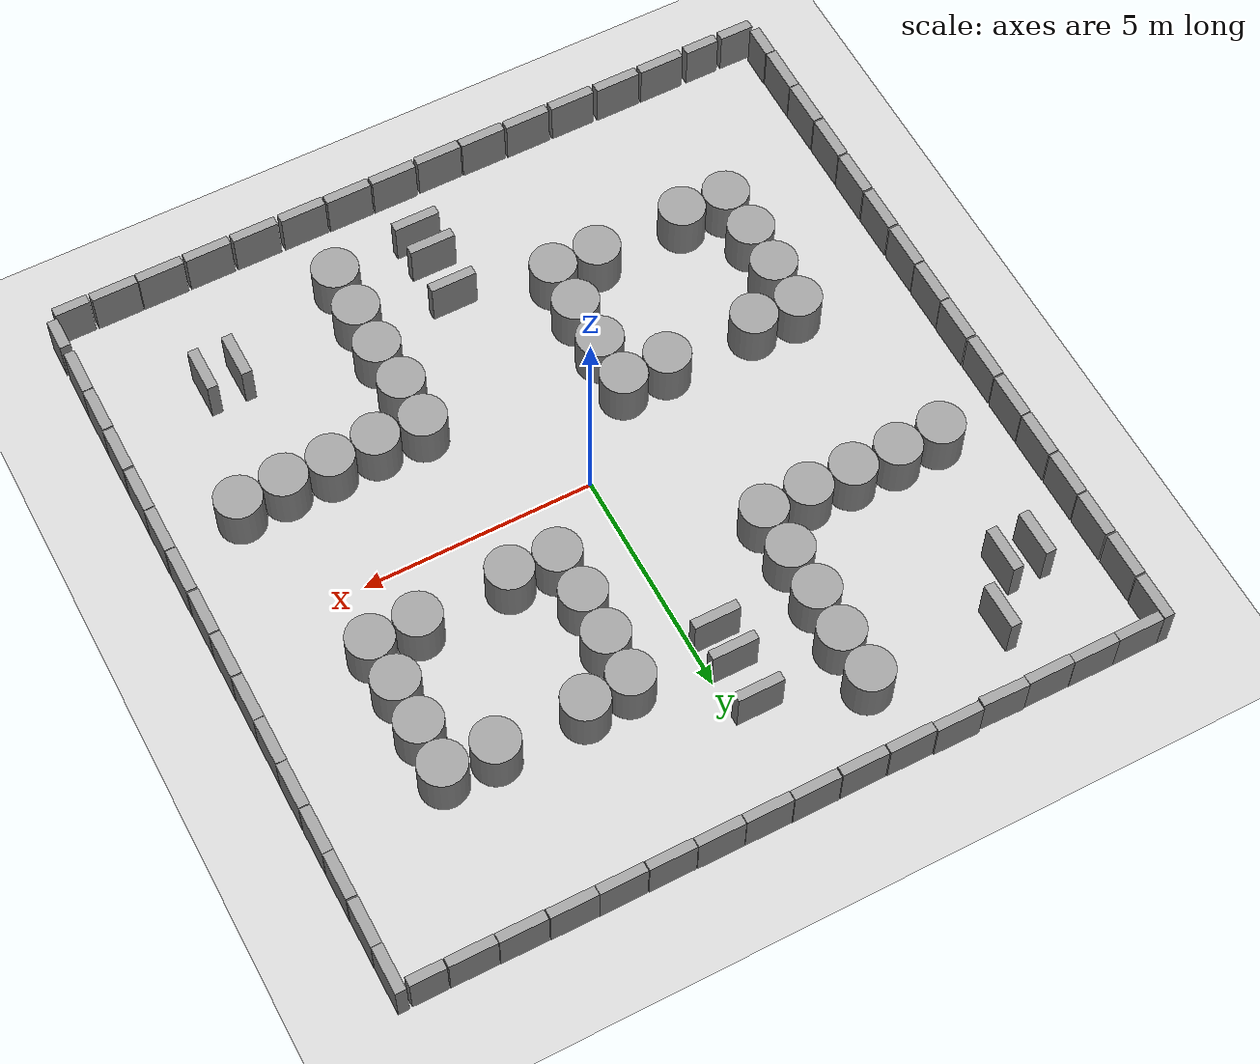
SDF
<sdf version="1.6">
 <world name="default">
  <light name="sun" type="directional">
   <pose>0 0 10 0 -0 0</pose>
   <diffuse>0.8 0.8 0.8 1</diffuse>
   <specular>0.1 0.1 0.1 1</specular>
   <attenuation>
    <range>1000</range>
    <constant>0.9</constant>
    <linear>0.01</linear>
    <quadratic>0.001</quadratic>
   </attenuation>
   <direction>-0.5 0.5 -1</direction>
  </light>
  <model name="ground_plane">
   <static>1</static>
   <static>1</static>
   <link name="link">
    <collision name="collision">
     <geometry><plane><normal>0 0 1</normal><size>100 100</size></plane></geometry>
     <surface><friction><ode><mu>100</mu><mu2>50</mu2></ode></friction></surface>
    </collision>
    <visual name="visual">
     <cast_shadows>0</cast_shadows>
     <geometry><plane><normal>0 0 1</normal><size>100 100</size></plane></geometry>
     <material>
      <script><uri>file://media/materials/scripts/gazebo.material</uri><name>Gazebo/Grey</name></script>
     </material>
    </visual>
   </link>
  </model>
  <gravity>0 0 -9.8</gravity>
  <magnetic_field>6e-06 2.3e-05 -4.2e-05</magnetic_field>
  <atmosphere type="adiabatic"/>
  <physics name="default_physics" default="0" type="ode">
   <max_step_size>0.001</max_step_size>
   <real_time_factor>1</real_time_factor>
   <real_time_update_rate>1000</real_time_update_rate>
  </physics>
  <scene><ambient>0.4 0.4 0.4 1</ambient><background>0.7 0.7 0.7 1</background><shadows>1</shadows></scene>
  <spherical_coordinates>
   <surface_model>EARTH_WGS84</surface_model>
   <latitude_deg>0</latitude_deg>
   <longitude_deg>0</longitude_deg>
   <elevation>0</elevation>
   <heading_deg>0</heading_deg>
  </spherical_coordinates>
  <audio><device>default</device></audio>
  <model name="unit_box_clone">
   <pose>-7.49845 8.11988 0.5 0 -0 0.000178</pose>
   <link name="link">
    <inertial>
     <mass>1</mass>
     <inertia>
      <ixx>0.166667</ixx>
      <ixy>0</ixy>
      <ixz>0</ixz>
      <iyy>0.166667</iyy>
      <iyz>0</iyz>
      <izz>0.166667</izz>
     </inertia>
    </inertial>
    <collision name="collision"><geometry><box><size>1 0.210541 1</size></box></geometry></collision>
    <visual name="visual">
     <geometry><box><size>1 0.210541 1</size></box></geometry>
     <material>
      <script><name>Gazebo/Grey</name><uri>file://media/materials/scripts/gazebo.material</uri></script>
     </material>
    </visual>
   </link>
  </model>
  <model name="unit_box_clone_0">
   <pose>-6.49729 8.11969 0.5 0 -1e-06 -0.002353</pose>
   <link name="link">
    <inertial>
     <mass>1</mass>
     <inertia>
      <ixx>0.166667</ixx>
      <ixy>0</ixy>
      <ixz>0</ixz>
      <iyy>0.166667</iyy>
      <iyz>0</iyz>
      <izz>0.166667</izz>
     </inertia>
    </inertial>
    <collision name="collision"><geometry><box><size>1 0.210541 1</size></box></geometry></collision>
    <visual name="visual">
     <geometry><box><size>1 0.210541 1</size></box></geometry>
     <material>
      <script><name>Gazebo/Grey</name><uri>file://media/materials/scripts/gazebo.material</uri></script>
     </material>
    </visual>
   </link>
  </model>
  <model name="unit_box_clone_1">
   <pose>-5.49732 8.10842 0.5 0 0 -0.002354</pose>
   <link name="link">
    <inertial>
     <mass>1</mass>
     <inertia>
      <ixx>0.166667</ixx>
      <ixy>0</ixy>
      <ixz>0</ixz>
      <iyy>0.166667</iyy>
      <iyz>0</iyz>
      <izz>0.166667</izz>
     </inertia>
    </inertial>
    <collision name="collision"><geometry><box><size>1 0.210541 1</size></box></geometry></collision>
    <visual name="visual">
     <geometry><box><size>1 0.210541 1</size></box></geometry>
     <material>
      <script><name>Gazebo/Grey</name><uri>file://media/materials/scripts/gazebo.material</uri></script>
     </material>
    </visual>
   </link>
  </model>
  <model name="unit_box_clone_2">
   <pose>-4.49485 8.1106 0.5 -0 -0 -0.02677</pose>
   <link name="link">
    <inertial>
     <mass>1</mass>
     <inertia>
      <ixx>0.166667</ixx>
      <ixy>0</ixy>
      <ixz>0</ixz>
      <iyy>0.166667</iyy>
      <iyz>0</iyz>
      <izz>0.166667</izz>
     </inertia>
    </inertial>
    <collision name="collision"><geometry><box><size>1 0.210541 1</size></box></geometry></collision>
    <visual name="visual">
     <geometry><box><size>1 0.210541 1</size></box></geometry>
     <material>
      <script><name>Gazebo/Grey</name><uri>file://media/materials/scripts/gazebo.material</uri></script>
     </material>
    </visual>
   </link>
  </model>
  <model name="unit_box_clone_3">
   <pose>-3.46835 8.1504 0.5 -1e-06 1e-06 -0.007775</pose>
   <link name="link">
    <inertial>
     <mass>1</mass>
     <inertia>
      <ixx>0.166667</ixx>
      <ixy>0</ixy>
      <ixz>0</ixz>
      <iyy>0.166667</iyy>
      <iyz>0</iyz>
      <izz>0.166667</izz>
     </inertia>
    </inertial>
    <collision name="collision"><geometry><box><size>1 0.210541 1</size></box></geometry></collision>
    <visual name="visual">
     <geometry><box><size>1 0.210541 1</size></box></geometry>
     <material>
      <script><name>Gazebo/Grey</name><uri>file://media/materials/scripts/gazebo.material</uri></script>
     </material>
    </visual>
   </link>
  </model>
  <model name="unit_box_clone_4">
   <pose>-2.46316 8.11857 0.5 0 -0 0.000178</pose>
   <link name="link">
    <inertial>
     <mass>1</mass>
     <inertia>
      <ixx>0.166667</ixx>
      <ixy>0</ixy>
      <ixz>0</ixz>
      <iyy>0.166667</iyy>
      <iyz>0</iyz>
      <izz>0.166667</izz>
     </inertia>
    </inertial>
    <collision name="collision"><geometry><box><size>1 0.210541 1</size></box></geometry></collision>
    <visual name="visual">
     <geometry><box><size>1 0.210541 1</size></box></geometry>
     <material>
      <script><name>Gazebo/Grey</name><uri>file://media/materials/scripts/gazebo.material</uri></script>
     </material>
    </visual>
   </link>
  </model>
  <model name="unit_box_clone_5">
   <pose>-1.44425 8.11191 0.5 0 -0 0.000178</pose>
   <link name="link">
    <inertial>
     <mass>1</mass>
     <inertia>
      <ixx>0.166667</ixx>
      <ixy>0</ixy>
      <ixz>0</ixz>
      <iyy>0.166667</iyy>
      <iyz>0</iyz>
      <izz>0.166667</izz>
     </inertia>
    </inertial>
    <collision name="collision"><geometry><box><size>1 0.210541 1</size></box></geometry></collision>
    <visual name="visual">
     <geometry><box><size>1 0.210541 1</size></box></geometry>
     <material>
      <script><name>Gazebo/Grey</name><uri>file://media/materials/scripts/gazebo.material</uri></script>
     </material>
    </visual>
   </link>
  </model>
  <model name="unit_box_clone_6">
   <pose>-0.418683 8.11856 0.5 0 -0 0.000178</pose>
   <link name="link">
    <inertial>
     <mass>1</mass>
     <inertia>
      <ixx>0.166667</ixx>
      <ixy>0</ixy>
      <ixz>0</ixz>
      <iyy>0.166667</iyy>
      <iyz>0</iyz>
      <izz>0.166667</izz>
     </inertia>
    </inertial>
    <collision name="collision"><geometry><box><size>1 0.210541 1</size></box></geometry></collision>
    <visual name="visual">
     <geometry><box><size>1 0.210541 1</size></box></geometry>
     <material>
      <script><name>Gazebo/Grey</name><uri>file://media/materials/scripts/gazebo.material</uri></script>
     </material>
    </visual>
   </link>
  </model>
  <model name="unit_box_clone_7">
   <pose>0.592836 8.11143 0.5 0 -0 0.000178</pose>
   <link name="link">
    <inertial>
     <mass>1</mass>
     <inertia>
      <ixx>0.166667</ixx>
      <ixy>0</ixy>
      <ixz>0</ixz>
      <iyy>0.166667</iyy>
      <iyz>0</iyz>
      <izz>0.166667</izz>
     </inertia>
    </inertial>
    <collision name="collision"><geometry><box><size>1 0.210541 1</size></box></geometry></collision>
    <visual name="visual">
     <geometry><box><size>1 0.210541 1</size></box></geometry>
     <material>
      <script><name>Gazebo/Grey</name><uri>file://media/materials/scripts/gazebo.material</uri></script>
     </material>
    </visual>
   </link>
  </model>
  <model name="unit_box_clone_8">
   <pose>1.60043 8.10994 0.5 0 -0 0.000178</pose>
   <link name="link">
    <inertial>
     <mass>1</mass>
     <inertia>
      <ixx>0.166667</ixx>
      <ixy>0</ixy>
      <ixz>0</ixz>
      <iyy>0.166667</iyy>
      <iyz>0</iyz>
      <izz>0.166667</izz>
     </inertia>
    </inertial>
    <collision name="collision"><geometry><box><size>1 0.210541 1</size></box></geometry></collision>
    <visual name="visual">
     <geometry><box><size>1 0.210541 1</size></box></geometry>
     <material>
      <script><name>Gazebo/Grey</name><uri>file://media/materials/scripts/gazebo.material</uri></script>
     </material>
    </visual>
   </link>
  </model>
  <model name="unit_box_clone_9">
   <pose>2.60987 8.10275 0.5 0 -0 0.000178</pose>
   <link name="link">
    <inertial>
     <mass>1</mass>
     <inertia>
      <ixx>0.166667</ixx>
      <ixy>0</ixy>
      <ixz>0</ixz>
      <iyy>0.166667</iyy>
      <iyz>0</iyz>
      <izz>0.166667</izz>
     </inertia>
    </inertial>
    <collision name="collision"><geometry><box><size>1 0.210541 1</size></box></geometry></collision>
    <visual name="visual">
     <geometry><box><size>1 0.210541 1</size></box></geometry>
     <material>
      <script><name>Gazebo/Grey</name><uri>file://media/materials/scripts/gazebo.material</uri></script>
     </material>
    </visual>
   </link>
  </model>
  <model name="unit_box_clone_10">
   <pose>3.62649 8.09916 0.5 0 -0 0.000178</pose>
   <link name="link">
    <inertial>
     <mass>1</mass>
     <inertia>
      <ixx>0.166667</ixx>
      <ixy>0</ixy>
      <ixz>0</ixz>
      <iyy>0.166667</iyy>
      <iyz>0</iyz>
      <izz>0.166667</izz>
     </inertia>
    </inertial>
    <collision name="collision"><geometry><box><size>1 0.210541 1</size></box></geometry></collision>
    <visual name="visual">
     <geometry><box><size>1 0.210541 1</size></box></geometry>
     <material>
      <script><name>Gazebo/Grey</name><uri>file://media/materials/scripts/gazebo.material</uri></script>
     </material>
    </visual>
   </link>
  </model>
  <model name="unit_box_clone_11">
   <pose>4.63309 8.09539 0.5 0 0 -0.003434</pose>
   <link name="link">
    <inertial>
     <mass>1</mass>
     <inertia>
      <ixx>0.166667</ixx>
      <ixy>0</ixy>
      <ixz>0</ixz>
      <iyy>0.166667</iyy>
      <iyz>0</iyz>
      <izz>0.166667</izz>
     </inertia>
    </inertial>
    <collision name="collision"><geometry><box><size>1 0.210541 1</size></box></geometry></collision>
    <visual name="visual">
     <geometry><box><size>1 0.210541 1</size></box></geometry>
     <material>
      <script><name>Gazebo/Grey</name><uri>file://media/materials/scripts/gazebo.material</uri></script>
     </material>
    </visual>
   </link>
  </model>
  <model name="unit_box_0_clone_0">
   <pose>8.11522 6.68458 0.5 -0 -0 -0.000239</pose>
   <link name="link">
    <inertial>
     <mass>1</mass>
     <inertia>
      <ixx>0.166667</ixx>
      <ixy>0</ixy>
      <ixz>0</ixz>
      <iyy>0.166667</iyy>
      <iyz>0</iyz>
      <izz>0.166667</izz>
     </inertia>
    </inertial>
    <collision name="collision"><geometry><box><size>0.230819 1 1</size></box></geometry></collision>
    <visual name="visual">
     <geometry><box><size>0.230819 1 1</size></box></geometry>
     <material>
      <script><name>Gazebo/Grey</name><uri>file://media/materials/scripts/gazebo.material</uri></script>
     </material>
    </visual>
   </link>
  </model>
  <model name="unit_box_0_clone_1">
   <pose>8.11915 5.6517 0.5 0 -0 0.000138</pose>
   <link name="link">
    <inertial>
     <mass>1</mass>
     <inertia>
      <ixx>0.166667</ixx>
      <ixy>0</ixy>
      <ixz>0</ixz>
      <iyy>0.166667</iyy>
      <iyz>0</iyz>
      <izz>0.166667</izz>
     </inertia>
    </inertial>
    <collision name="collision"><geometry><box><size>0.230819 1 1</size></box></geometry></collision>
    <visual name="visual">
     <geometry><box><size>0.230819 1 1</size></box></geometry>
     <material>
      <script><name>Gazebo/Grey</name><uri>file://media/materials/scripts/gazebo.material</uri></script>
     </material>
    </visual>
   </link>
  </model>
  <model name="unit_box_0_clone_2">
   <pose>8.11914 4.64016 0.5 0 -0 0.000232</pose>
   <link name="link">
    <inertial>
     <mass>1</mass>
     <inertia>
      <ixx>0.166667</ixx>
      <ixy>0</ixy>
      <ixz>0</ixz>
      <iyy>0.166667</iyy>
      <iyz>0</iyz>
      <izz>0.166667</izz>
     </inertia>
    </inertial>
    <collision name="collision"><geometry><box><size>0.230819 1 1</size></box></geometry></collision>
    <visual name="visual">
     <geometry><box><size>0.230819 1 1</size></box></geometry>
     <material>
      <script><name>Gazebo/Grey</name><uri>file://media/materials/scripts/gazebo.material</uri></script>
     </material>
    </visual>
   </link>
  </model>
  <model name="unit_box_0_clone_3">
   <pose>8.11914 3.62228 0.5 0 -0 0.000213</pose>
   <link name="link">
    <inertial>
     <mass>1</mass>
     <inertia>
      <ixx>0.166667</ixx>
      <ixy>0</ixy>
      <ixz>0</ixz>
      <iyy>0.166667</iyy>
      <iyz>0</iyz>
      <izz>0.166667</izz>
     </inertia>
    </inertial>
    <collision name="collision"><geometry><box><size>0.230819 1 1</size></box></geometry></collision>
    <visual name="visual">
     <geometry><box><size>0.230819 1 1</size></box></geometry>
     <material>
      <script><name>Gazebo/Grey</name><uri>file://media/materials/scripts/gazebo.material</uri></script>
     </material>
    </visual>
   </link>
  </model>
  <model name="unit_box_0_clone_4">
   <pose>8.11332 2.61063 0.5 0 0 -0.001021</pose>
   <link name="link">
    <inertial>
     <mass>1</mass>
     <inertia>
      <ixx>0.166667</ixx>
      <ixy>0</ixy>
      <ixz>0</ixz>
      <iyy>0.166667</iyy>
      <iyz>0</iyz>
      <izz>0.166667</izz>
     </inertia>
    </inertial>
    <collision name="collision"><geometry><box><size>0.230819 1 1</size></box></geometry></collision>
    <visual name="visual">
     <geometry><box><size>0.230819 1 1</size></box></geometry>
     <material>
      <script><name>Gazebo/Grey</name><uri>file://media/materials/scripts/gazebo.material</uri></script>
     </material>
    </visual>
   </link>
  </model>
  <model name="unit_box_0_clone_5">
   <pose>8.11277 1.59919 0.5 0 -0 0.000213</pose>
   <link name="link">
    <inertial>
     <mass>1</mass>
     <inertia>
      <ixx>0.166667</ixx>
      <ixy>0</ixy>
      <ixz>0</ixz>
      <iyy>0.166667</iyy>
      <iyz>0</iyz>
      <izz>0.166667</izz>
     </inertia>
    </inertial>
    <collision name="collision"><geometry><box><size>0.230819 1 1</size></box></geometry></collision>
    <visual name="visual">
     <geometry><box><size>0.230819 1 1</size></box></geometry>
     <material>
      <script><name>Gazebo/Grey</name><uri>file://media/materials/scripts/gazebo.material</uri></script>
     </material>
    </visual>
   </link>
  </model>
  <model name="unit_box_0_clone_6">
   <pose>8.11277 0.574938 0.5 0 -0 0.000213</pose>
   <link name="link">
    <inertial>
     <mass>1</mass>
     <inertia>
      <ixx>0.166667</ixx>
      <ixy>0</ixy>
      <ixz>0</ixz>
      <iyy>0.166667</iyy>
      <iyz>0</iyz>
      <izz>0.166667</izz>
     </inertia>
    </inertial>
    <collision name="collision"><geometry><box><size>0.230819 1 1</size></box></geometry></collision>
    <visual name="visual">
     <geometry><box><size>0.230819 1 1</size></box></geometry>
     <material>
      <script><name>Gazebo/Grey</name><uri>file://media/materials/scripts/gazebo.material</uri></script>
     </material>
    </visual>
   </link>
  </model>
  <model name="unit_box_0_clone_7">
   <pose>8.11276 -0.44932 0.5 0 -0 0.000213</pose>
   <link name="link">
    <inertial>
     <mass>1</mass>
     <inertia>
      <ixx>0.166667</ixx>
      <ixy>0</ixy>
      <ixz>0</ixz>
      <iyy>0.166667</iyy>
      <iyz>0</iyz>
      <izz>0.166667</izz>
     </inertia>
    </inertial>
    <collision name="collision"><geometry><box><size>0.230819 1 1</size></box></geometry></collision>
    <visual name="visual">
     <geometry><box><size>0.230819 1 1</size></box></geometry>
     <material>
      <script><name>Gazebo/Grey</name><uri>file://media/materials/scripts/gazebo.material</uri></script>
     </material>
    </visual>
   </link>
  </model>
  <model name="unit_box_0_clone_8">
   <pose>8.11912 -1.48629 0.5 0 -0 0.000213</pose>
   <link name="link">
    <inertial>
     <mass>1</mass>
     <inertia>
      <ixx>0.166667</ixx>
      <ixy>0</ixy>
      <ixz>0</ixz>
      <iyy>0.166667</iyy>
      <iyz>0</iyz>
      <izz>0.166667</izz>
     </inertia>
    </inertial>
    <collision name="collision"><geometry><box><size>0.230819 1 1</size></box></geometry></collision>
    <visual name="visual">
     <geometry><box><size>0.230819 1 1</size></box></geometry>
     <material>
      <script><name>Gazebo/Grey</name><uri>file://media/materials/scripts/gazebo.material</uri></script>
     </material>
    </visual>
   </link>
  </model>
  <model name="unit_box_0_clone_9">
   <pose>8.12548 -2.5042 0.5 0 -0 0.000213</pose>
   <link name="link">
    <inertial>
     <mass>1</mass>
     <inertia>
      <ixx>0.166667</ixx>
      <ixy>0</ixy>
      <ixz>0</ixz>
      <iyy>0.166667</iyy>
      <iyz>0</iyz>
      <izz>0.166667</izz>
     </inertia>
    </inertial>
    <collision name="collision"><geometry><box><size>0.230819 1 1</size></box></geometry></collision>
    <visual name="visual">
     <geometry><box><size>0.230819 1 1</size></box></geometry>
     <material>
      <script><name>Gazebo/Grey</name><uri>file://media/materials/scripts/gazebo.material</uri></script>
     </material>
    </visual>
   </link>
  </model>
  <model name="unit_box_0_clone_10">
   <pose>8.12331 -3.52223 0.5 0 -0 0.000213</pose>
   <link name="link">
    <inertial>
     <mass>1</mass>
     <inertia>
      <ixx>0.166667</ixx>
      <ixy>0</ixy>
      <ixz>0</ixz>
      <iyy>0.166667</iyy>
      <iyz>0</iyz>
      <izz>0.166667</izz>
     </inertia>
    </inertial>
    <collision name="collision"><geometry><box><size>0.230819 1 1</size></box></geometry></collision>
    <visual name="visual">
     <geometry><box><size>0.230819 1 1</size></box></geometry>
     <material>
      <script><name>Gazebo/Grey</name><uri>file://media/materials/scripts/gazebo.material</uri></script>
     </material>
    </visual>
   </link>
  </model>
  <model name="unit_box_0_clone_11">
   <pose>8.1233 -4.56316 0.5 0 -0 0.000213</pose>
   <link name="link">
    <inertial>
     <mass>1</mass>
     <inertia>
      <ixx>0.166667</ixx>
      <ixy>0</ixy>
      <ixz>0</ixz>
      <iyy>0.166667</iyy>
      <iyz>0</iyz>
      <izz>0.166667</izz>
     </inertia>
    </inertial>
    <collision name="collision"><geometry><box><size>0.230819 1 1</size></box></geometry></collision>
    <visual name="visual">
     <geometry><box><size>0.230819 1 1</size></box></geometry>
     <material>
      <script><name>Gazebo/Grey</name><uri>file://media/materials/scripts/gazebo.material</uri></script>
     </material>
    </visual>
   </link>
  </model>
  <model name="unit_box_0_clone_12">
   <pose>8.11815 -5.59377 0.5 0 -0 0.000213</pose>
   <link name="link">
    <inertial>
     <mass>1</mass>
     <inertia>
      <ixx>0.166667</ixx>
      <ixy>0</ixy>
      <ixz>0</ixz>
      <iyy>0.166667</iyy>
      <iyz>0</iyz>
      <izz>0.166667</izz>
     </inertia>
    </inertial>
    <collision name="collision"><geometry><box><size>0.230819 1 1</size></box></geometry></collision>
    <visual name="visual">
     <geometry><box><size>0.230819 1 1</size></box></geometry>
     <material>
      <script><name>Gazebo/Grey</name><uri>file://media/materials/scripts/gazebo.material</uri></script>
     </material>
    </visual>
   </link>
  </model>
  <model name="unit_box_0_clone_13">
   <pose>8.11333 -6.60776 0.5 0 0 -0.005399</pose>
   <link name="link">
    <inertial>
     <mass>1</mass>
     <inertia>
      <ixx>0.166667</ixx>
      <ixy>0</ixy>
      <ixz>0</ixz>
      <iyy>0.166667</iyy>
      <iyz>0</iyz>
      <izz>0.166667</izz>
     </inertia>
    </inertial>
    <collision name="collision"><geometry><box><size>0.230819 1 1</size></box></geometry></collision>
    <visual name="visual">
     <geometry><box><size>0.230819 1 1</size></box></geometry>
     <material>
      <script><name>Gazebo/Grey</name><uri>file://media/materials/scripts/gazebo.material</uri></script>
     </material>
    </visual>
   </link>
  </model>
  <model name="unit_box_clone_15_clone_0">
   <pose>6.71207 -8.13116 0.5 0 -0 0.000178</pose>
   <link name="link">
    <inertial>
     <mass>1</mass>
     <inertia>
      <ixx>0.166667</ixx>
      <ixy>0</ixy>
      <ixz>0</ixz>
      <iyy>0.166667</iyy>
      <iyz>0</iyz>
      <izz>0.166667</izz>
     </inertia>
    </inertial>
    <collision name="collision"><geometry><box><size>1 0.210541 1</size></box></geometry></collision>
    <visual name="visual">
     <geometry><box><size>1 0.210541 1</size></box></geometry>
     <material>
      <script><name>Gazebo/Grey</name><uri>file://media/materials/scripts/gazebo.material</uri></script>
     </material>
    </visual>
   </link>
  </model>
  <model name="unit_box_clone_15_clone_1">
   <pose>5.69715 -8.13115 0.5 0 -0 0.000178</pose>
   <link name="link">
    <inertial>
     <mass>1</mass>
     <inertia>
      <ixx>0.166667</ixx>
      <ixy>0</ixy>
      <ixz>0</ixz>
      <iyy>0.166667</iyy>
      <iyz>0</iyz>
      <izz>0.166667</izz>
     </inertia>
    </inertial>
    <collision name="collision"><geometry><box><size>1 0.210541 1</size></box></geometry></collision>
    <visual name="visual">
     <geometry><box><size>1 0.210541 1</size></box></geometry>
     <material>
      <script><name>Gazebo/Grey</name><uri>file://media/materials/scripts/gazebo.material</uri></script>
     </material>
    </visual>
   </link>
  </model>
  <model name="unit_box_clone_15_clone_2">
   <pose>4.63881 -8.13733 0.5 0 -0 0.000178</pose>
   <link name="link">
    <inertial>
     <mass>1</mass>
     <inertia>
      <ixx>0.166667</ixx>
      <ixy>0</ixy>
      <ixz>0</ixz>
      <iyy>0.166667</iyy>
      <iyz>0</iyz>
      <izz>0.166667</izz>
     </inertia>
    </inertial>
    <collision name="collision"><geometry><box><size>1 0.210541 1</size></box></geometry></collision>
    <visual name="visual">
     <geometry><box><size>1 0.210541 1</size></box></geometry>
     <material>
      <script><name>Gazebo/Grey</name><uri>file://media/materials/scripts/gazebo.material</uri></script>
     </material>
    </visual>
   </link>
  </model>
  <model name="unit_box_clone_15_clone_3">
   <pose>3.57975 -8.13733 0.5 0 -0 0.000178</pose>
   <link name="link">
    <inertial>
     <mass>1</mass>
     <inertia>
      <ixx>0.166667</ixx>
      <ixy>0</ixy>
      <ixz>0</ixz>
      <iyy>0.166667</iyy>
      <iyz>0</iyz>
      <izz>0.166667</izz>
     </inertia>
    </inertial>
    <collision name="collision"><geometry><box><size>1 0.210541 1</size></box></geometry></collision>
    <visual name="visual">
     <geometry><box><size>1 0.210541 1</size></box></geometry>
     <material>
      <script><name>Gazebo/Grey</name><uri>file://media/materials/scripts/gazebo.material</uri></script>
     </material>
    </visual>
   </link>
  </model>
  <model name="unit_box_clone_15_clone_4">
   <pose>2.49815 -8.13732 0.5 0 -0 0.000178</pose>
   <link name="link">
    <inertial>
     <mass>1</mass>
     <inertia>
      <ixx>0.166667</ixx>
      <ixy>0</ixy>
      <ixz>0</ixz>
      <iyy>0.166667</iyy>
      <iyz>0</iyz>
      <izz>0.166667</izz>
     </inertia>
    </inertial>
    <collision name="collision"><geometry><box><size>1 0.210541 1</size></box></geometry></collision>
    <visual name="visual">
     <geometry><box><size>1 0.210541 1</size></box></geometry>
     <material>
      <script><name>Gazebo/Grey</name><uri>file://media/materials/scripts/gazebo.material</uri></script>
     </material>
    </visual>
   </link>
  </model>
  <model name="unit_box_clone_15_clone_5">
   <pose>1.46162 -8.12605 0.5 0 -0 0.000178</pose>
   <link name="link">
    <inertial>
     <mass>1</mass>
     <inertia>
      <ixx>0.166667</ixx>
      <ixy>0</ixy>
      <ixz>0</ixz>
      <iyy>0.166667</iyy>
      <iyz>0</iyz>
      <izz>0.166667</izz>
     </inertia>
    </inertial>
    <collision name="collision"><geometry><box><size>1 0.210541 1</size></box></geometry></collision>
    <visual name="visual">
     <geometry><box><size>1 0.210541 1</size></box></geometry>
     <material>
      <script><name>Gazebo/Grey</name><uri>file://media/materials/scripts/gazebo.material</uri></script>
     </material>
    </visual>
   </link>
  </model>
  <model name="unit_box_clone_15_clone_6">
   <pose>0.425089 -8.12604 0.5 0 -0 0.000178</pose>
   <link name="link">
    <inertial>
     <mass>1</mass>
     <inertia>
      <ixx>0.166667</ixx>
      <ixy>0</ixy>
      <ixz>0</ixz>
      <iyy>0.166667</iyy>
      <iyz>0</iyz>
      <izz>0.166667</izz>
     </inertia>
    </inertial>
    <collision name="collision"><geometry><box><size>1 0.210541 1</size></box></geometry></collision>
    <visual name="visual">
     <geometry><box><size>1 0.210541 1</size></box></geometry>
     <material>
      <script><name>Gazebo/Grey</name><uri>file://media/materials/scripts/gazebo.material</uri></script>
     </material>
    </visual>
   </link>
  </model>
  <model name="unit_box_clone_15_clone_7">
   <pose>-0.633973 -8.14859 0.5 0 -0 0.000178</pose>
   <link name="link">
    <inertial>
     <mass>1</mass>
     <inertia>
      <ixx>0.166667</ixx>
      <ixy>0</ixy>
      <ixz>0</ixz>
      <iyy>0.166667</iyy>
      <iyz>0</iyz>
      <izz>0.166667</izz>
     </inertia>
    </inertial>
    <collision name="collision"><geometry><box><size>1 0.210541 1</size></box></geometry></collision>
    <visual name="visual">
     <geometry><box><size>1 0.210541 1</size></box></geometry>
     <material>
      <script><name>Gazebo/Grey</name><uri>file://media/materials/scripts/gazebo.material</uri></script>
     </material>
    </visual>
   </link>
  </model>
  <model name="unit_box_clone_15_clone_8">
   <pose>-1.65923 -8.13731 0.5 0 -0 0.000178</pose>
   <link name="link">
    <inertial>
     <mass>1</mass>
     <inertia>
      <ixx>0.166667</ixx>
      <ixy>0</ixy>
      <ixz>0</ixz>
      <iyy>0.166667</iyy>
      <iyz>0</iyz>
      <izz>0.166667</izz>
     </inertia>
    </inertial>
    <collision name="collision"><geometry><box><size>1 0.210541 1</size></box></geometry></collision>
    <visual name="visual">
     <geometry><box><size>1 0.210541 1</size></box></geometry>
     <material>
      <script><name>Gazebo/Grey</name><uri>file://media/materials/scripts/gazebo.material</uri></script>
     </material>
    </visual>
   </link>
  </model>
  <model name="unit_box_clone_15_clone_9">
   <pose>-2.70703 -8.12606 0.5 0 -0 0.000178</pose>
   <link name="link">
    <inertial>
     <mass>1</mass>
     <inertia>
      <ixx>0.166667</ixx>
      <ixy>0</ixy>
      <ixz>0</ixz>
      <iyy>0.166667</iyy>
      <iyz>0</iyz>
      <izz>0.166667</izz>
     </inertia>
    </inertial>
    <collision name="collision"><geometry><box><size>1 0.210541 1</size></box></geometry></collision>
    <visual name="visual">
     <geometry><box><size>1 0.210541 1</size></box></geometry>
     <material>
      <script><name>Gazebo/Grey</name><uri>file://media/materials/scripts/gazebo.material</uri></script>
     </material>
    </visual>
   </link>
  </model>
  <model name="unit_box_clone_15_clone_10">
   <pose>-3.77736 -8.12605 0.5 0 -0 0.000178</pose>
   <link name="link">
    <inertial>
     <mass>1</mass>
     <inertia>
      <ixx>0.166667</ixx>
      <ixy>0</ixy>
      <ixz>0</ixz>
      <iyy>0.166667</iyy>
      <iyz>0</iyz>
      <izz>0.166667</izz>
     </inertia>
    </inertial>
    <collision name="collision"><geometry><box><size>1 0.210541 1</size></box></geometry></collision>
    <visual name="visual">
     <geometry><box><size>1 0.210541 1</size></box></geometry>
     <material>
      <script><name>Gazebo/Grey</name><uri>file://media/materials/scripts/gazebo.material</uri></script>
     </material>
    </visual>
   </link>
  </model>
  <model name="unit_box_clone_15_clone_11">
   <pose>-4.85896 -8.11479 0.5 0 -0 0.000178</pose>
   <link name="link">
    <inertial>
     <mass>1</mass>
     <inertia>
      <ixx>0.166667</ixx>
      <ixy>0</ixy>
      <ixz>0</ixz>
      <iyy>0.166667</iyy>
      <iyz>0</iyz>
      <izz>0.166667</izz>
     </inertia>
    </inertial>
    <collision name="collision"><geometry><box><size>1 0.210541 1</size></box></geometry></collision>
    <visual name="visual">
     <geometry><box><size>1 0.210541 1</size></box></geometry>
     <material>
      <script><name>Gazebo/Grey</name><uri>file://media/materials/scripts/gazebo.material</uri></script>
     </material>
    </visual>
   </link>
  </model>
  <model name="unit_box_clone_15_clone_12">
   <pose>-5.91802 -8.11478 0.5 0 -0 0.000178</pose>
   <link name="link">
    <inertial>
     <mass>1</mass>
     <inertia>
      <ixx>0.166667</ixx>
      <ixy>0</ixy>
      <ixz>0</ixz>
      <iyy>0.166667</iyy>
      <iyz>0</iyz>
      <izz>0.166667</izz>
     </inertia>
    </inertial>
    <collision name="collision"><geometry><box><size>1 0.210541 1</size></box></geometry></collision>
    <visual name="visual">
     <geometry><box><size>1 0.210541 1</size></box></geometry>
     <material>
      <script><name>Gazebo/Grey</name><uri>file://media/materials/scripts/gazebo.material</uri></script>
     </material>
    </visual>
   </link>
  </model>
  <model name="unit_box_0_clone_4_clone">
   <pose>-8.12647 7.71769 0.5 0 -0 0.000213</pose>
   <link name="link">
    <inertial>
     <mass>1</mass>
     <inertia>
      <ixx>0.166667</ixx>
      <ixy>0</ixy>
      <ixz>0</ixz>
      <iyy>0.166667</iyy>
      <iyz>0</iyz>
      <izz>0.166667</izz>
     </inertia>
    </inertial>
    <collision name="collision"><geometry><box><size>0.230819 1 1</size></box></geometry></collision>
    <visual name="visual">
     <geometry><box><size>0.230819 1 1</size></box></geometry>
     <material>
      <script><name>Gazebo/Grey</name><uri>file://media/materials/scripts/gazebo.material</uri></script>
     </material>
    </visual>
   </link>
  </model>
  <model name="unit_box_0_clone_4_clone_0">
   <pose>-8.13281 6.68715 0.5 0 -0 0.000213</pose>
   <link name="link">
    <inertial>
     <mass>1</mass>
     <inertia>
      <ixx>0.166667</ixx>
      <ixy>0</ixy>
      <ixz>0</ixz>
      <iyy>0.166667</iyy>
      <iyz>0</iyz>
      <izz>0.166667</izz>
     </inertia>
    </inertial>
    <collision name="collision"><geometry><box><size>0.230819 1 1</size></box></geometry></collision>
    <visual name="visual">
     <geometry><box><size>0.230819 1 1</size></box></geometry>
     <material>
      <script><name>Gazebo/Grey</name><uri>file://media/materials/scripts/gazebo.material</uri></script>
     </material>
    </visual>
   </link>
  </model>
  <model name="unit_box_0_clone_4_clone_1">
   <pose>-8.12606 5.64722 0.5 0 -0 0.000213</pose>
   <link name="link">
    <inertial>
     <mass>1</mass>
     <inertia>
      <ixx>0.166667</ixx>
      <ixy>0</ixy>
      <ixz>0</ixz>
      <iyy>0.166667</iyy>
      <iyz>0</iyz>
      <izz>0.166667</izz>
     </inertia>
    </inertial>
    <collision name="collision"><geometry><box><size>0.230819 1 1</size></box></geometry></collision>
    <visual name="visual">
     <geometry><box><size>0.230819 1 1</size></box></geometry>
     <material>
      <script><name>Gazebo/Grey</name><uri>file://media/materials/scripts/gazebo.material</uri></script>
     </material>
    </visual>
   </link>
  </model>
  <model name="unit_box_0_clone_4_clone_2">
   <pose>-8.12607 4.6208 0.5 0 -0 0.000213</pose>
   <link name="link">
    <inertial>
     <mass>1</mass>
     <inertia>
      <ixx>0.166667</ixx>
      <ixy>0</ixy>
      <ixz>0</ixz>
      <iyy>0.166667</iyy>
      <iyz>0</iyz>
      <izz>0.166667</izz>
     </inertia>
    </inertial>
    <collision name="collision"><geometry><box><size>0.230819 1 1</size></box></geometry></collision>
    <visual name="visual">
     <geometry><box><size>0.230819 1 1</size></box></geometry>
     <material>
      <script><name>Gazebo/Grey</name><uri>file://media/materials/scripts/gazebo.material</uri></script>
     </material>
    </visual>
   </link>
  </model>
  <model name="unit_box_0_clone_4_clone_3">
   <pose>-8.11932 3.59437 0.5 0 -0 0.000213</pose>
   <link name="link">
    <inertial>
     <mass>1</mass>
     <inertia>
      <ixx>0.166667</ixx>
      <ixy>0</ixy>
      <ixz>0</ixz>
      <iyy>0.166667</iyy>
      <iyz>0</iyz>
      <izz>0.166667</izz>
     </inertia>
    </inertial>
    <collision name="collision"><geometry><box><size>0.230819 1 1</size></box></geometry></collision>
    <visual name="visual">
     <geometry><box><size>0.230819 1 1</size></box></geometry>
     <material>
      <script><name>Gazebo/Grey</name><uri>file://media/materials/scripts/gazebo.material</uri></script>
     </material>
    </visual>
   </link>
  </model>
  <model name="unit_box_0_clone_4_clone_4">
   <pose>-8.11932 2.57471 0.5 0 -0 0.000213</pose>
   <link name="link">
    <inertial>
     <mass>1</mass>
     <inertia>
      <ixx>0.166667</ixx>
      <ixy>0</ixy>
      <ixz>0</ixz>
      <iyy>0.166667</iyy>
      <iyz>0</iyz>
      <izz>0.166667</izz>
     </inertia>
    </inertial>
    <collision name="collision"><geometry><box><size>0.230819 1 1</size></box></geometry></collision>
    <visual name="visual">
     <geometry><box><size>0.230819 1 1</size></box></geometry>
     <material>
      <script><name>Gazebo/Grey</name><uri>file://media/materials/scripts/gazebo.material</uri></script>
     </material>
    </visual>
   </link>
  </model>
  <model name="unit_box_0_clone_4_clone_5">
   <pose>-8.12608 1.54157 0.5 0 -0 0.000213</pose>
   <link name="link">
    <inertial>
     <mass>1</mass>
     <inertia>
      <ixx>0.166667</ixx>
      <ixy>0</ixy>
      <ixz>0</ixz>
      <iyy>0.166667</iyy>
      <iyz>0</iyz>
      <izz>0.166667</izz>
     </inertia>
    </inertial>
    <collision name="collision"><geometry><box><size>0.230819 1 1</size></box></geometry></collision>
    <visual name="visual">
     <geometry><box><size>0.230819 1 1</size></box></geometry>
     <material>
      <script><name>Gazebo/Grey</name><uri>file://media/materials/scripts/gazebo.material</uri></script>
     </material>
    </visual>
   </link>
  </model>
  <model name="unit_box_0_clone_4_clone_6">
   <pose>-8.11933 0.50163 0.5 0 -0 0.000213</pose>
   <link name="link">
    <inertial>
     <mass>1</mass>
     <inertia>
      <ixx>0.166667</ixx>
      <ixy>0</ixy>
      <ixz>0</ixz>
      <iyy>0.166667</iyy>
      <iyz>0</iyz>
      <izz>0.166667</izz>
     </inertia>
    </inertial>
    <collision name="collision"><geometry><box><size>0.230819 1 1</size></box></geometry></collision>
    <visual name="visual">
     <geometry><box><size>0.230819 1 1</size></box></geometry>
     <material>
      <script><name>Gazebo/Grey</name><uri>file://media/materials/scripts/gazebo.material</uri></script>
     </material>
    </visual>
   </link>
  </model>
  <model name="unit_box_0_clone_4_clone_7">
   <pose>-8.12609 -0.518034 0.5 0 -0 0.000213</pose>
   <link name="link">
    <inertial>
     <mass>1</mass>
     <inertia>
      <ixx>0.166667</ixx>
      <ixy>0</ixy>
      <ixz>0</ixz>
      <iyy>0.166667</iyy>
      <iyz>0</iyz>
      <izz>0.166667</izz>
     </inertia>
    </inertial>
    <collision name="collision"><geometry><box><size>0.230819 1 1</size></box></geometry></collision>
    <visual name="visual">
     <geometry><box><size>0.230819 1 1</size></box></geometry>
     <material>
      <script><name>Gazebo/Grey</name><uri>file://media/materials/scripts/gazebo.material</uri></script>
     </material>
    </visual>
   </link>
  </model>
  <model name="unit_box_0_clone_4_clone_8">
   <pose>-8.13284 -1.54445 0.5 0 -0 0.000213</pose>
   <link name="link">
    <inertial>
     <mass>1</mass>
     <inertia>
      <ixx>0.166667</ixx>
      <ixy>0</ixy>
      <ixz>0</ixz>
      <iyy>0.166667</iyy>
      <iyz>0</iyz>
      <izz>0.166667</izz>
     </inertia>
    </inertial>
    <collision name="collision"><geometry><box><size>0.230819 1 1</size></box></geometry></collision>
    <visual name="visual">
     <geometry><box><size>0.230819 1 1</size></box></geometry>
     <material>
      <script><name>Gazebo/Grey</name><uri>file://media/materials/scripts/gazebo.material</uri></script>
     </material>
    </visual>
   </link>
  </model>
  <model name="unit_box_0_clone_4_clone_9">
   <pose>-8.13285 -2.58439 0.5 0 -0 0.000213</pose>
   <link name="link">
    <inertial>
     <mass>1</mass>
     <inertia>
      <ixx>0.166667</ixx>
      <ixy>0</ixy>
      <ixz>0</ixz>
      <iyy>0.166667</iyy>
      <iyz>0</iyz>
      <izz>0.166667</izz>
     </inertia>
    </inertial>
    <collision name="collision"><geometry><box><size>0.230819 1 1</size></box></geometry></collision>
    <visual name="visual">
     <geometry><box><size>0.230819 1 1</size></box></geometry>
     <material>
      <script><name>Gazebo/Grey</name><uri>file://media/materials/scripts/gazebo.material</uri></script>
     </material>
    </visual>
   </link>
  </model>
  <model name="unit_box_0_clone_4_clone_10">
   <pose>-8.13285 -3.62431 0.5 0 -0 0.000213</pose>
   <link name="link">
    <inertial>
     <mass>1</mass>
     <inertia>
      <ixx>0.166667</ixx>
      <ixy>0</ixy>
      <ixz>0</ixz>
      <iyy>0.166667</iyy>
      <iyz>0</iyz>
      <izz>0.166667</izz>
     </inertia>
    </inertial>
    <collision name="collision"><geometry><box><size>0.230819 1 1</size></box></geometry></collision>
    <visual name="visual">
     <geometry><box><size>0.230819 1 1</size></box></geometry>
     <material>
      <script><name>Gazebo/Grey</name><uri>file://media/materials/scripts/gazebo.material</uri></script>
     </material>
    </visual>
   </link>
  </model>
  <model name="unit_box_0_clone_4_clone_11">
   <pose>-8.1396 -4.65747 0.5 0 -0 0.000213</pose>
   <link name="link">
    <inertial>
     <mass>1</mass>
     <inertia>
      <ixx>0.166667</ixx>
      <ixy>0</ixy>
      <ixz>0</ixz>
      <iyy>0.166667</iyy>
      <iyz>0</iyz>
      <izz>0.166667</izz>
     </inertia>
    </inertial>
    <collision name="collision"><geometry><box><size>0.230819 1 1</size></box></geometry></collision>
    <visual name="visual">
     <geometry><box><size>0.230819 1 1</size></box></geometry>
     <material>
      <script><name>Gazebo/Grey</name><uri>file://media/materials/scripts/gazebo.material</uri></script>
     </material>
    </visual>
   </link>
  </model>
  <model name="unit_box_0_clone_4_clone_12">
   <pose>-8.1396 -5.69064 0.5 0 -0 0.000213</pose>
   <link name="link">
    <inertial>
     <mass>1</mass>
     <inertia>
      <ixx>0.166667</ixx>
      <ixy>0</ixy>
      <ixz>0</ixz>
      <iyy>0.166667</iyy>
      <iyz>0</iyz>
      <izz>0.166667</izz>
     </inertia>
    </inertial>
    <collision name="collision"><geometry><box><size>0.230819 1 1</size></box></geometry></collision>
    <visual name="visual">
     <geometry><box><size>0.230819 1 1</size></box></geometry>
     <material>
      <script><name>Gazebo/Grey</name><uri>file://media/materials/scripts/gazebo.material</uri></script>
     </material>
    </visual>
   </link>
  </model>
  <model name="unit_box_0_clone_4_clone_13">
   <pose>-8.14113 -6.70874 0.5 -0 -0 -0.008612</pose>
   <link name="link">
    <inertial>
     <mass>1</mass>
     <inertia>
      <ixx>0.166667</ixx>
      <ixy>0</ixy>
      <ixz>0</ixz>
      <iyy>0.166667</iyy>
      <iyz>0</iyz>
      <izz>0.166667</izz>
     </inertia>
    </inertial>
    <collision name="collision"><geometry><box><size>0.230819 1 1</size></box></geometry></collision>
    <visual name="visual">
     <geometry><box><size>0.230819 1 1</size></box></geometry>
     <material>
      <script><name>Gazebo/Grey</name><uri>file://media/materials/scripts/gazebo.material</uri></script>
     </material>
    </visual>
   </link>
  </model>
  <model name="unit_box_0_clone_0_clone">
   <pose>8.11438 7.69322 0.5 0 -0 0.00012</pose>
   <link name="link">
    <inertial>
     <mass>1</mass>
     <inertia>
      <ixx>0.166667</ixx>
      <ixy>0</ixy>
      <ixz>0</ixz>
      <iyy>0.166667</iyy>
      <iyz>0</iyz>
      <izz>0.166667</izz>
     </inertia>
    </inertial>
    <collision name="collision"><geometry><box><size>0.230819 1 1</size></box></geometry></collision>
    <visual name="visual">
     <geometry><box><size>0.230819 1 1</size></box></geometry>
     <material>
      <script><name>Gazebo/Grey</name><uri>file://media/materials/scripts/gazebo.material</uri></script>
     </material>
    </visual>
   </link>
  </model>
  <model name="unit_box_clone_11_clone">
   <pose>5.6544 8.08375 0.5 1e-06 -1e-06 -0.0029</pose>
   <link name="link">
    <inertial>
     <mass>1</mass>
     <inertia>
      <ixx>0.166667</ixx>
      <ixy>0</ixy>
      <ixz>0</ixz>
      <iyy>0.166667</iyy>
      <iyz>0</iyz>
      <izz>0.166667</izz>
     </inertia>
    </inertial>
    <collision name="collision"><geometry><box><size>1 0.210541 1</size></box></geometry></collision>
    <visual name="visual">
     <geometry><box><size>1 0.210541 1</size></box></geometry>
     <material>
      <script><name>Gazebo/Grey</name><uri>file://media/materials/scripts/gazebo.material</uri></script>
     </material>
    </visual>
   </link>
  </model>
  <model name="unit_box_clone_11_clone_0">
   <pose>6.66439 8.07358 0.5 0 0 -0.003356</pose>
   <link name="link">
    <inertial>
     <mass>1</mass>
     <inertia>
      <ixx>0.166667</ixx>
      <ixy>0</ixy>
      <ixz>0</ixz>
      <iyy>0.166667</iyy>
      <iyz>0</iyz>
      <izz>0.166667</izz>
     </inertia>
    </inertial>
    <collision name="collision"><geometry><box><size>1 0.210541 1</size></box></geometry></collision>
    <visual name="visual">
     <geometry><box><size>1 0.210541 1</size></box></geometry>
     <material>
      <script><name>Gazebo/Grey</name><uri>file://media/materials/scripts/gazebo.material</uri></script>
     </material>
    </visual>
   </link>
  </model>
  <model name="unit_box_clone_11_clone_1_clone">
   <pose>7.56439 8.07324 0.5 0 1e-06 -0.004927</pose>
   <link name="link">
    <inertial>
     <mass>1</mass>
     <inertia>
      <ixx>0.166667</ixx>
      <ixy>0</ixy>
      <ixz>0</ixz>
      <iyy>0.166667</iyy>
      <iyz>0</iyz>
      <izz>0.166667</izz>
     </inertia>
    </inertial>
    <collision name="collision"><geometry><box><size>0.750223 0.210541 1</size></box></geometry></collision>
    <visual name="visual">
     <geometry><box><size>0.750223 0.210541 1</size></box></geometry>
     <material>
      <script><name>Gazebo/Grey</name><uri>file://media/materials/scripts/gazebo.material</uri></script>
     </material>
    </visual>
   </link>
  </model>
  <model name="unit_box_clone_11_clone_1_clone_0">
   <pose>-6.9088 -8.11956 0.499997 -2e-06 7e-06 -0.002394</pose>
   <link name="link">
    <inertial>
     <mass>1</mass>
     <inertia>
      <ixx>0.166667</ixx>
      <ixy>0</ixy>
      <ixz>0</ixz>
      <iyy>0.166667</iyy>
      <iyz>0</iyz>
      <izz>0.166667</izz>
     </inertia>
    </inertial>
    <collision name="collision"><geometry><box><size>0.750223 0.210541 1</size></box></geometry></collision>
    <visual name="visual">
     <geometry><box><size>0.750223 0.210541 1</size></box></geometry>
     <material>
      <script><name>Gazebo/Grey</name><uri>file://media/materials/scripts/gazebo.material</uri></script>
     </material>
    </visual>
   </link>
  </model>
  <model name="unit_box_0_clone_4_clone_13_clone_clone">
   <pose>-8.13833 -7.57661 0.499997 7e-06 3e-06 -0.014396</pose>
   <link name="link">
    <inertial>
     <mass>1</mass>
     <inertia>
      <ixx>0.166667</ixx>
      <ixy>0</ixy>
      <ixz>0</ixz>
      <iyy>0.166667</iyy>
      <iyz>0</iyz>
      <izz>0.166667</izz>
     </inertia>
    </inertial>
    <collision name="collision"><geometry><box><size>0.230819 0.700336 1</size></box></geometry></collision>
    <visual name="visual">
     <geometry><box><size>0.230819 0.700336 1</size></box></geometry>
     <material>
      <script><name>Gazebo/Grey</name><uri>file://media/materials/scripts/gazebo.material</uri></script>
     </material>
    </visual>
   </link>
  </model>
  <model name="unit_box_clone_11_clone_1_clone_0_clone">
   <pose>-7.75474 -8.12201 0.499997 2e-06 8e-06 -0.008367</pose>
   <link name="link">
    <inertial>
     <mass>1</mass>
     <inertia>
      <ixx>0.166667</ixx>
      <ixy>0</ixy>
      <ixz>0</ixz>
      <iyy>0.166667</iyy>
      <iyz>0</iyz>
      <izz>0.166667</izz>
     </inertia>
    </inertial>
    <collision name="collision"><geometry><box><size>0.750223 0.210541 1</size></box></geometry></collision>
    <visual name="visual">
     <geometry><box><size>0.750223 0.210541 1</size></box></geometry>
     <material>
      <script><name>Gazebo/Grey</name><uri>file://media/materials/scripts/gazebo.material</uri></script>
     </material>
    </visual>
   </link>
  </model>
  <model name="unit_box_clone_11_clone_1_clone_2">
   <pose>7.64248 -8.13929 0.499997 2e-06 -7e-06 -0.000572</pose>
   <link name="link">
    <inertial>
     <mass>1</mass>
     <inertia>
      <ixx>0.166667</ixx>
      <ixy>0</ixy>
      <ixz>0</ixz>
      <iyy>0.166667</iyy>
      <iyz>0</iyz>
      <izz>0.166667</izz>
     </inertia>
    </inertial>
    <collision name="collision"><geometry><box><size>0.750223 0.210541 1</size></box></geometry></collision>
    <visual name="visual">
     <geometry><box><size>0.750223 0.210541 1</size></box></geometry>
     <material>
      <script><name>Gazebo/Grey</name><uri>file://media/materials/scripts/gazebo.material</uri></script>
     </material>
    </visual>
   </link>
  </model>
  <model name="unit_box_0_clone_4_clone_13_clone_clone_clone">
   <pose>8.11859 -7.62156 0.499997 7e-06 -2e-06 -0.004126</pose>
   <link name="link">
    <inertial>
     <mass>1</mass>
     <inertia>
      <ixx>0.166667</ixx>
      <ixy>0</ixy>
      <ixz>0</ixz>
      <iyy>0.166667</iyy>
      <iyz>0</iyz>
      <izz>0.166667</izz>
     </inertia>
    </inertial>
    <collision name="collision"><geometry><box><size>0.230819 0.700336 1</size></box></geometry></collision>
    <visual name="visual">
     <geometry><box><size>0.230819 0.700336 1</size></box></geometry>
     <material>
      <script><name>Gazebo/Grey</name><uri>file://media/materials/scripts/gazebo.material</uri></script>
     </material>
    </visual>
   </link>
  </model>
  <model name="unit_cylinder_clone_0_clone">
   <pose>1.51726 1.4877 0.499991 -0 -0 -0.002488</pose>
   <link name="link">
    <inertial>
     <mass>1</mass>
     <inertia><ixx>0.145833</ixx><ixy>0</ixy><ixz>0</ixz><iyy>0.145833</iyy><iyz>0</iyz><izz>0.125</izz></inertia>
    </inertial>
    <collision name="collision">
     <geometry><cylinder><radius>0.5</radius><length>1</length></cylinder></geometry>
    </collision>
    <visual name="visual">
     <geometry><cylinder><radius>0.5</radius><length>1</length></cylinder></geometry>
     <material>
      <script><name>Gazebo/Grey</name><uri>file://media/materials/scripts/gazebo.material</uri></script>
     </material>
    </visual>
   </link>
  </model>
  <model name="unit_cylinder_clone_0_clone_clone">
   <pose>1.48343 2.4873 0.499994 -3e-06 -1e-06 0.000788</pose>
   <link name="link">
    <inertial>
     <mass>1</mass>
     <inertia><ixx>0.145833</ixx><ixy>0</ixy><ixz>0</ixz><iyy>0.145833</iyy><iyz>0</iyz><izz>0.125</izz></inertia>
    </inertial>
    <collision name="collision">
     <geometry><cylinder><radius>0.5</radius><length>1</length></cylinder></geometry>
    </collision>
    <visual name="visual">
     <geometry><cylinder><radius>0.5</radius><length>1</length></cylinder></geometry>
     <material>
      <script><name>Gazebo/Grey</name><uri>file://media/materials/scripts/gazebo.material</uri></script>
     </material>
    </visual>
   </link>
  </model>
  <model name="unit_cylinder_clone_0_clone_clone_0">
   <pose>1.51714 3.48917 0.499994 -4e-06 -3e-06 0.000101</pose>
   <link name="link">
    <inertial>
     <mass>1</mass>
     <inertia><ixx>0.145833</ixx><ixy>0</ixy><ixz>0</ixz><iyy>0.145833</iyy><iyz>0</iyz><izz>0.125</izz></inertia>
    </inertial>
    <collision name="collision">
     <geometry><cylinder><radius>0.5</radius><length>1</length></cylinder></geometry>
    </collision>
    <visual name="visual">
     <geometry><cylinder><radius>0.5</radius><length>1</length></cylinder></geometry>
     <material>
      <script><name>Gazebo/Grey</name><uri>file://media/materials/scripts/gazebo.material</uri></script>
     </material>
    </visual>
   </link>
  </model>
  <model name="unit_cylinder_clone_0_clone_clone_1">
   <pose>1.51681 4.48917 0.5 0 0 -0.0001</pose>
   <link name="link">
    <inertial>
     <mass>1</mass>
     <inertia><ixx>0.145833</ixx><ixy>0</ixy><ixz>0</ixz><iyy>0.145833</iyy><iyz>0</iyz><izz>0.125</izz></inertia>
    </inertial>
    <collision name="collision">
     <geometry><cylinder><radius>0.5</radius><length>1</length></cylinder></geometry>
    </collision>
    <visual name="visual">
     <geometry><cylinder><radius>0.5</radius><length>1</length></cylinder></geometry>
     <material>
      <script><name>Gazebo/Grey</name><uri>file://media/materials/scripts/gazebo.material</uri></script>
     </material>
    </visual>
   </link>
  </model>
  <model name="unit_cylinder_clone_0_clone_clone_2">
   <pose>2.51555 1.41016 0.499994 -3e-06 -2e-06 -0.003965</pose>
   <link name="link">
    <inertial>
     <mass>1</mass>
     <inertia><ixx>0.145833</ixx><ixy>0</ixy><ixz>0</ixz><iyy>0.145833</iyy><iyz>0</iyz><izz>0.125</izz></inertia>
    </inertial>
    <collision name="collision">
     <geometry><cylinder><radius>0.5</radius><length>1</length></cylinder></geometry>
    </collision>
    <visual name="visual">
     <geometry><cylinder><radius>0.5</radius><length>1</length></cylinder></geometry>
     <material>
      <script><name>Gazebo/Grey</name><uri>file://media/materials/scripts/gazebo.material</uri></script>
     </material>
    </visual>
   </link>
  </model>
  <model name="unit_cylinder_clone_0_clone_clone_3">
   <pose>4.52533 1.49818 0.499994 -3e-06 -2e-06 0</pose>
   <link name="link">
    <inertial>
     <mass>1</mass>
     <inertia><ixx>0.145833</ixx><ixy>0</ixy><ixz>0</ixz><iyy>0.145833</iyy><iyz>0</iyz><izz>0.125</izz></inertia>
    </inertial>
    <collision name="collision">
     <geometry><cylinder><radius>0.5</radius><length>1</length></cylinder></geometry>
    </collision>
    <visual name="visual">
     <geometry><cylinder><radius>0.5</radius><length>1</length></cylinder></geometry>
     <material>
      <script><name>Gazebo/Grey</name><uri>file://media/materials/scripts/gazebo.material</uri></script>
     </material>
    </visual>
   </link>
  </model>
  <model name="unit_cylinder_clone_0_clone_clone_4">
   <pose>5.54013 1.51656 0.499996 -1e-06 0 -0.000814</pose>
   <link name="link">
    <inertial>
     <mass>1</mass>
     <inertia><ixx>0.145833</ixx><ixy>0</ixy><ixz>0</ixz><iyy>0.145833</iyy><iyz>0</iyz><izz>0.125</izz></inertia>
    </inertial>
    <collision name="collision">
     <geometry><cylinder><radius>0.5</radius><length>1</length></cylinder></geometry>
    </collision>
    <visual name="visual">
     <geometry><cylinder><radius>0.5</radius><length>1</length></cylinder></geometry>
     <material>
      <script><name>Gazebo/Grey</name><uri>file://media/materials/scripts/gazebo.material</uri></script>
     </material>
    </visual>
   </link>
  </model>
  <model name="unit_cylinder_clone_0_clone_clone_5">
   <pose>5.48689 2.51519 0.499997 3e-06 2e-06 0.000368</pose>
   <link name="link">
    <inertial>
     <mass>1</mass>
     <inertia><ixx>0.145833</ixx><ixy>0</ixy><ixz>0</ixz><iyy>0.145833</iyy><iyz>0</iyz><izz>0.125</izz></inertia>
    </inertial>
    <collision name="collision">
     <geometry><cylinder><radius>0.5</radius><length>1</length></cylinder></geometry>
    </collision>
    <visual name="visual">
     <geometry><cylinder><radius>0.5</radius><length>1</length></cylinder></geometry>
     <material>
      <script><name>Gazebo/Grey</name><uri>file://media/materials/scripts/gazebo.material</uri></script>
     </material>
    </visual>
   </link>
  </model>
  <model name="unit_cylinder_clone_0_clone_clone_6">
   <pose>5.488 3.51524 0.499993 -3e-06 1e-06 0.000266</pose>
   <link name="link">
    <inertial>
     <mass>1</mass>
     <inertia><ixx>0.145833</ixx><ixy>0</ixy><ixz>0</ixz><iyy>0.145833</iyy><iyz>0</iyz><izz>0.125</izz></inertia>
    </inertial>
    <collision name="collision">
     <geometry><cylinder><radius>0.5</radius><length>1</length></cylinder></geometry>
    </collision>
    <visual name="visual">
     <geometry><cylinder><radius>0.5</radius><length>1</length></cylinder></geometry>
     <material>
      <script><name>Gazebo/Grey</name><uri>file://media/materials/scripts/gazebo.material</uri></script>
     </material>
    </visual>
   </link>
  </model>
  <model name="unit_cylinder_clone_0_clone_clone_7">
   <pose>5.48818 4.51568 0.5 0 -0 0.001132</pose>
   <link name="link">
    <inertial>
     <mass>1</mass>
     <inertia><ixx>0.145833</ixx><ixy>0</ixy><ixz>0</ixz><iyy>0.145833</iyy><iyz>0</iyz><izz>0.125</izz></inertia>
    </inertial>
    <collision name="collision">
     <geometry><cylinder><radius>0.5</radius><length>1</length></cylinder></geometry>
    </collision>
    <visual name="visual">
     <geometry><cylinder><radius>0.5</radius><length>1</length></cylinder></geometry>
     <material>
      <script><name>Gazebo/Grey</name><uri>file://media/materials/scripts/gazebo.material</uri></script>
     </material>
    </visual>
   </link>
  </model>
  <model name="unit_cylinder_clone_0_clone_clone_8">
   <pose>2.51446 4.55792 0.49999 0 -0 -6.8e-05</pose>
   <link name="link">
    <inertial>
     <mass>1</mass>
     <inertia><ixx>0.145833</ixx><ixy>0</ixy><ixz>0</ixz><iyy>0.145833</iyy><iyz>0</iyz><izz>0.125</izz></inertia>
    </inertial>
    <collision name="collision">
     <geometry><cylinder><radius>0.5</radius><length>1</length></cylinder></geometry>
    </collision>
    <visual name="visual">
     <geometry><cylinder><radius>0.5</radius><length>1</length></cylinder></geometry>
     <material>
      <script><name>Gazebo/Grey</name><uri>file://media/materials/scripts/gazebo.material</uri></script>
     </material>
    </visual>
   </link>
  </model>
  <model name="unit_cylinder_clone_0_clone_clone_9">
   <pose>4.40502 4.5579 0.499997 4e-06 3e-06 -0</pose>
   <link name="link">
    <inertial>
     <mass>1</mass>
     <inertia><ixx>0.145833</ixx><ixy>0</ixy><ixz>0</ixz><iyy>0.145833</iyy><iyz>0</iyz><izz>0.125</izz></inertia>
    </inertial>
    <collision name="collision">
     <geometry><cylinder><radius>0.5</radius><length>1</length></cylinder></geometry>
    </collision>
    <visual name="visual">
     <geometry><cylinder><radius>0.5</radius><length>1</length></cylinder></geometry>
     <material>
      <script><name>Gazebo/Grey</name><uri>file://media/materials/scripts/gazebo.material</uri></script>
     </material>
    </visual>
   </link>
  </model>
  <model name="unit_cylinder_clone_0_clone_clone_10">
   <pose>-1.52214 -1.49115 0.499994 -1e-06 -0 0.000478</pose>
   <link name="link">
    <inertial>
     <mass>1</mass>
     <inertia><ixx>0.145833</ixx><ixy>0</ixy><ixz>0</ixz><iyy>0.145833</iyy><iyz>0</iyz><izz>0.125</izz></inertia>
    </inertial>
    <collision name="collision">
     <geometry><cylinder><radius>0.5</radius><length>1</length></cylinder></geometry>
    </collision>
    <visual name="visual">
     <geometry><cylinder><radius>0.5</radius><length>1</length></cylinder></geometry>
     <material>
      <script><name>Gazebo/Grey</name><uri>file://media/materials/scripts/gazebo.material</uri></script>
     </material>
    </visual>
   </link>
  </model>
  <model name="unit_cylinder_clone_0_clone_clone_11">
   <pose>-2.52198 -1.51033 0.499996 3e-06 1e-06 0.00022</pose>
   <link name="link">
    <inertial>
     <mass>1</mass>
     <inertia><ixx>0.145833</ixx><ixy>0</ixy><ixz>0</ixz><iyy>0.145833</iyy><iyz>0</iyz><izz>0.125</izz></inertia>
    </inertial>
    <collision name="collision">
     <geometry><cylinder><radius>0.5</radius><length>1</length></cylinder></geometry>
    </collision>
    <visual name="visual">
     <geometry><cylinder><radius>0.5</radius><length>1</length></cylinder></geometry>
     <material>
      <script><name>Gazebo/Grey</name><uri>file://media/materials/scripts/gazebo.material</uri></script>
     </material>
    </visual>
   </link>
  </model>
  <model name="unit_cylinder_clone_0_clone_clone_12">
   <pose>-4.53006 -1.52762 0.499998 1e-06 1e-06 -0.000988</pose>
   <link name="link">
    <inertial>
     <mass>1</mass>
     <inertia><ixx>0.145833</ixx><ixy>0</ixy><ixz>0</ixz><iyy>0.145833</iyy><iyz>0</iyz><izz>0.125</izz></inertia>
    </inertial>
    <collision name="collision">
     <geometry><cylinder><radius>0.5</radius><length>1</length></cylinder></geometry>
    </collision>
    <visual name="visual">
     <geometry><cylinder><radius>0.5</radius><length>1</length></cylinder></geometry>
     <material>
      <script><name>Gazebo/Grey</name><uri>file://media/materials/scripts/gazebo.material</uri></script>
     </material>
    </visual>
   </link>
  </model>
  <model name="unit_cylinder_clone_0_clone_clone_13">
   <pose>-5.52941 -1.47557 0.499991 0 -0 -0.000236</pose>
   <link name="link">
    <inertial>
     <mass>1</mass>
     <inertia><ixx>0.145833</ixx><ixy>0</ixy><ixz>0</ixz><iyy>0.145833</iyy><iyz>0</iyz><izz>0.125</izz></inertia>
    </inertial>
    <collision name="collision">
     <geometry><cylinder><radius>0.5</radius><length>1</length></cylinder></geometry>
    </collision>
    <visual name="visual">
     <geometry><cylinder><radius>0.5</radius><length>1</length></cylinder></geometry>
     <material>
      <script><name>Gazebo/Grey</name><uri>file://media/materials/scripts/gazebo.material</uri></script>
     </material>
    </visual>
   </link>
  </model>
  <model name="unit_cylinder_clone_0_clone_clone_14">
   <pose>-5.5297 -2.47581 0.499991 0 -0 -0.000142</pose>
   <link name="link">
    <inertial>
     <mass>1</mass>
     <inertia><ixx>0.145833</ixx><ixy>0</ixy><ixz>0</ixz><iyy>0.145833</iyy><iyz>0</iyz><izz>0.125</izz></inertia>
    </inertial>
    <collision name="collision">
     <geometry><cylinder><radius>0.5</radius><length>1</length></cylinder></geometry>
    </collision>
    <visual name="visual">
     <geometry><cylinder><radius>0.5</radius><length>1</length></cylinder></geometry>
     <material>
      <script><name>Gazebo/Grey</name><uri>file://media/materials/scripts/gazebo.material</uri></script>
     </material>
    </visual>
   </link>
  </model>
  <model name="unit_cylinder_clone_0_clone_clone_15">
   <pose>-5.5485 -3.47564 0.5 0 -0 -0.000202</pose>
   <link name="link">
    <inertial>
     <mass>1</mass>
     <inertia><ixx>0.145833</ixx><ixy>0</ixy><ixz>0</ixz><iyy>0.145833</iyy><iyz>0</iyz><izz>0.125</izz></inertia>
    </inertial>
    <collision name="collision">
     <geometry><cylinder><radius>0.5</radius><length>1</length></cylinder></geometry>
    </collision>
    <visual name="visual">
     <geometry><cylinder><radius>0.5</radius><length>1</length></cylinder></geometry>
     <material>
      <script><name>Gazebo/Grey</name><uri>file://media/materials/scripts/gazebo.material</uri></script>
     </material>
    </visual>
   </link>
  </model>
  <model name="unit_cylinder_clone_0_clone_clone_16">
   <pose>-5.51723 -4.48236 0.499997 3e-06 1e-06 -0.000117</pose>
   <link name="link">
    <inertial>
     <mass>1</mass>
     <inertia><ixx>0.145833</ixx><ixy>0</ixy><ixz>0</ixz><iyy>0.145833</iyy><iyz>0</iyz><izz>0.125</izz></inertia>
    </inertial>
    <collision name="collision">
     <geometry><cylinder><radius>0.5</radius><length>1</length></cylinder></geometry>
    </collision>
    <visual name="visual">
     <geometry><cylinder><radius>0.5</radius><length>1</length></cylinder></geometry>
     <material>
      <script><name>Gazebo/Grey</name><uri>file://media/materials/scripts/gazebo.material</uri></script>
     </material>
    </visual>
   </link>
  </model>
  <model name="unit_cylinder_clone_0_clone_clone_17">
   <pose>-4.51968 -4.55258 0.5 0 -0 0.001021</pose>
   <link name="link">
    <inertial>
     <mass>1</mass>
     <inertia><ixx>0.145833</ixx><ixy>0</ixy><ixz>0</ixz><iyy>0.145833</iyy><iyz>0</iyz><izz>0.125</izz></inertia>
    </inertial>
    <collision name="collision">
     <geometry><cylinder><radius>0.5</radius><length>1</length></cylinder></geometry>
    </collision>
    <visual name="visual">
     <geometry><cylinder><radius>0.5</radius><length>1</length></cylinder></geometry>
     <material>
      <script><name>Gazebo/Grey</name><uri>file://media/materials/scripts/gazebo.material</uri></script>
     </material>
    </visual>
   </link>
  </model>
  <model name="unit_cylinder_clone_0_clone_clone_18">
   <pose>-2.49811 -4.50103 0.499993 -3e-06 -1e-06 5.2e-05</pose>
   <link name="link">
    <inertial>
     <mass>1</mass>
     <inertia><ixx>0.145833</ixx><ixy>0</ixy><ixz>0</ixz><iyy>0.145833</iyy><iyz>0</iyz><izz>0.125</izz></inertia>
    </inertial>
    <collision name="collision">
     <geometry><cylinder><radius>0.5</radius><length>1</length></cylinder></geometry>
    </collision>
    <visual name="visual">
     <geometry><cylinder><radius>0.5</radius><length>1</length></cylinder></geometry>
     <material>
      <script><name>Gazebo/Grey</name><uri>file://media/materials/scripts/gazebo.material</uri></script>
     </material>
    </visual>
   </link>
  </model>
  <model name="unit_cylinder_clone_0_clone_clone_19">
   <pose>-1.49826 -4.51946 0.499991 -0 -0 -0.000291</pose>
   <link name="link">
    <inertial>
     <mass>1</mass>
     <inertia><ixx>0.145833</ixx><ixy>0</ixy><ixz>0</ixz><iyy>0.145833</iyy><iyz>0</iyz><izz>0.125</izz></inertia>
    </inertial>
    <collision name="collision">
     <geometry><cylinder><radius>0.5</radius><length>1</length></cylinder></geometry>
    </collision>
    <visual name="visual">
     <geometry><cylinder><radius>0.5</radius><length>1</length></cylinder></geometry>
     <material>
      <script><name>Gazebo/Grey</name><uri>file://media/materials/scripts/gazebo.material</uri></script>
     </material>
    </visual>
   </link>
  </model>
  <model name="unit_cylinder_clone_0_clone_clone_20">
   <pose>-1.49057 -3.51931 0.499994 -3e-06 -1e-06 0.000551</pose>
   <link name="link">
    <inertial>
     <mass>1</mass>
     <inertia><ixx>0.145833</ixx><ixy>0</ixy><ixz>0</ixz><iyy>0.145833</iyy><iyz>0</iyz><izz>0.125</izz></inertia>
    </inertial>
    <collision name="collision">
     <geometry><cylinder><radius>0.5</radius><length>1</length></cylinder></geometry>
    </collision>
    <visual name="visual">
     <geometry><cylinder><radius>0.5</radius><length>1</length></cylinder></geometry>
     <material>
      <script><name>Gazebo/Grey</name><uri>file://media/materials/scripts/gazebo.material</uri></script>
     </material>
    </visual>
   </link>
  </model>
  <model name="unit_cylinder_clone_0_clone_clone_21">
   <pose>-1.50817 -2.49106 0.5 0 -0 -2e-05</pose>
   <link name="link">
    <inertial>
     <mass>1</mass>
     <inertia><ixx>0.145833</ixx><ixy>0</ixy><ixz>0</ixz><iyy>0.145833</iyy><iyz>0</iyz><izz>0.125</izz></inertia>
    </inertial>
    <collision name="collision">
     <geometry><cylinder><radius>0.5</radius><length>1</length></cylinder></geometry>
    </collision>
    <visual name="visual">
     <geometry><cylinder><radius>0.5</radius><length>1</length></cylinder></geometry>
     <material>
      <script><name>Gazebo/Grey</name><uri>file://media/materials/scripts/gazebo.material</uri></script>
     </material>
    </visual>
   </link>
  </model>
  <model name="unit_cylinder_clone_0_clone_clone_22">
   <pose>-2.49486 2.50135 0.5 0 -0 0.000104</pose>
   <link name="link">
    <inertial>
     <mass>1</mass>
     <inertia><ixx>0.145833</ixx><ixy>0</ixy><ixz>0</ixz><iyy>0.145833</iyy><iyz>0</iyz><izz>0.125</izz></inertia>
    </inertial>
    <collision name="collision">
     <geometry><cylinder><radius>0.5</radius><length>1</length></cylinder></geometry>
    </collision>
    <visual name="visual">
     <geometry><cylinder><radius>0.5</radius><length>1</length></cylinder></geometry>
     <material>
      <script><name>Gazebo/Grey</name><uri>file://media/materials/scripts/gazebo.material</uri></script>
     </material>
    </visual>
   </link>
  </model>
  <model name="unit_cylinder_clone_0_clone_clone_23">
   <pose>-2.51011 3.50155 0.5 0 0 -0.0023</pose>
   <link name="link">
    <inertial>
     <mass>1</mass>
     <inertia><ixx>0.145833</ixx><ixy>0</ixy><ixz>0</ixz><iyy>0.145833</iyy><iyz>0</iyz><izz>0.125</izz></inertia>
    </inertial>
    <collision name="collision">
     <geometry><cylinder><radius>0.5</radius><length>1</length></cylinder></geometry>
    </collision>
    <visual name="visual">
     <geometry><cylinder><radius>0.5</radius><length>1</length></cylinder></geometry>
     <material>
      <script><name>Gazebo/Grey</name><uri>file://media/materials/scripts/gazebo.material</uri></script>
     </material>
    </visual>
   </link>
  </model>
  <model name="unit_cylinder_clone_0_clone_clone_24">
   <pose>-2.51056 4.52097 0.5 0 0 -0.00241</pose>
   <link name="link">
    <inertial>
     <mass>1</mass>
     <inertia><ixx>0.145833</ixx><ixy>0</ixy><ixz>0</ixz><iyy>0.145833</iyy><iyz>0</iyz><izz>0.125</izz></inertia>
    </inertial>
    <collision name="collision">
     <geometry><cylinder><radius>0.5</radius><length>1</length></cylinder></geometry>
    </collision>
    <visual name="visual">
     <geometry><cylinder><radius>0.5</radius><length>1</length></cylinder></geometry>
     <material>
      <script><name>Gazebo/Grey</name><uri>file://media/materials/scripts/gazebo.material</uri></script>
     </material>
    </visual>
   </link>
  </model>
  <model name="unit_cylinder_clone_0_clone_clone_25">
   <pose>-2.47871 5.52049 0.499994 -4e-06 -1e-06 -0.002611</pose>
   <link name="link">
    <inertial>
     <mass>1</mass>
     <inertia><ixx>0.145833</ixx><ixy>0</ixy><ixz>0</ixz><iyy>0.145833</iyy><iyz>0</iyz><izz>0.125</izz></inertia>
    </inertial>
    <collision name="collision">
     <geometry><cylinder><radius>0.5</radius><length>1</length></cylinder></geometry>
    </collision>
    <visual name="visual">
     <geometry><cylinder><radius>0.5</radius><length>1</length></cylinder></geometry>
     <material>
      <script><name>Gazebo/Grey</name><uri>file://media/materials/scripts/gazebo.material</uri></script>
     </material>
    </visual>
   </link>
  </model>
  <model name="unit_cylinder_clone_0_clone_clone_26">
   <pose>-3.51621 2.46848 0.499997 -4e-06 -2e-06 -0.002536</pose>
   <link name="link">
    <inertial>
     <mass>1</mass>
     <inertia><ixx>0.145833</ixx><ixy>0</ixy><ixz>0</ixz><iyy>0.145833</iyy><iyz>0</iyz><izz>0.125</izz></inertia>
    </inertial>
    <collision name="collision">
     <geometry><cylinder><radius>0.5</radius><length>1</length></cylinder></geometry>
    </collision>
    <visual name="visual">
     <geometry><cylinder><radius>0.5</radius><length>1</length></cylinder></geometry>
     <material>
      <script><name>Gazebo/Grey</name><uri>file://media/materials/scripts/gazebo.material</uri></script>
     </material>
    </visual>
   </link>
  </model>
  <model name="unit_cylinder_clone_0_clone_clone_27">
   <pose>-4.5161 2.4837 0.499994 -3e-06 -2e-06 -0.002365</pose>
   <link name="link">
    <inertial>
     <mass>1</mass>
     <inertia><ixx>0.145833</ixx><ixy>0</ixy><ixz>0</ixz><iyy>0.145833</iyy><iyz>0</iyz><izz>0.125</izz></inertia>
    </inertial>
    <collision name="collision">
     <geometry><cylinder><radius>0.5</radius><length>1</length></cylinder></geometry>
    </collision>
    <visual name="visual">
     <geometry><cylinder><radius>0.5</radius><length>1</length></cylinder></geometry>
     <material>
      <script><name>Gazebo/Grey</name><uri>file://media/materials/scripts/gazebo.material</uri></script>
     </material>
    </visual>
   </link>
  </model>
  <model name="unit_cylinder_clone_0_clone_clone_28">
   <pose>-5.53031 2.49907 0.499997 1e-06 -1e-06 -0.002544</pose>
   <link name="link">
    <inertial>
     <mass>1</mass>
     <inertia><ixx>0.145833</ixx><ixy>0</ixy><ixz>0</ixz><iyy>0.145833</iyy><iyz>0</iyz><izz>0.125</izz></inertia>
    </inertial>
    <collision name="collision">
     <geometry><cylinder><radius>0.5</radius><length>1</length></cylinder></geometry>
    </collision>
    <visual name="visual">
     <geometry><cylinder><radius>0.5</radius><length>1</length></cylinder></geometry>
     <material>
      <script><name>Gazebo/Grey</name><uri>file://media/materials/scripts/gazebo.material</uri></script>
     </material>
    </visual>
   </link>
  </model>
  <model name="unit_cylinder_clone_0_clone_clone_29">
   <pose>-6.52989 2.46832 0.499992 -3e-06 -4e-06 -0.002494</pose>
   <link name="link">
    <inertial>
     <mass>1</mass>
     <inertia><ixx>0.145833</ixx><ixy>0</ixy><ixz>0</ixz><iyy>0.145833</iyy><iyz>0</iyz><izz>0.125</izz></inertia>
    </inertial>
    <collision name="collision">
     <geometry><cylinder><radius>0.5</radius><length>1</length></cylinder></geometry>
    </collision>
    <visual name="visual">
     <geometry><cylinder><radius>0.5</radius><length>1</length></cylinder></geometry>
     <material>
      <script><name>Gazebo/Grey</name><uri>file://media/materials/scripts/gazebo.material</uri></script>
     </material>
    </visual>
   </link>
  </model>
  <model name="unit_cylinder_clone_0_clone_clone_30">
   <pose>-2.52543 6.51942 0.499991 -0 -0 -0.002592</pose>
   <link name="link">
    <inertial>
     <mass>1</mass>
     <inertia><ixx>0.145833</ixx><ixy>0</ixy><ixz>0</ixz><iyy>0.145833</iyy><iyz>0</iyz><izz>0.125</izz></inertia>
    </inertial>
    <collision name="collision">
     <geometry><cylinder><radius>0.5</radius><length>1</length></cylinder></geometry>
    </collision>
    <visual name="visual">
     <geometry><cylinder><radius>0.5</radius><length>1</length></cylinder></geometry>
     <material>
      <script><name>Gazebo/Grey</name><uri>file://media/materials/scripts/gazebo.material</uri></script>
     </material>
    </visual>
   </link>
  </model>
  <model name="unit_cylinder_clone_0_clone_clone_31">
   <pose>2.4736 -2.46954 0.499997 3e-06 2e-06 -0.002503</pose>
   <link name="link">
    <inertial>
     <mass>1</mass>
     <inertia><ixx>0.145833</ixx><ixy>0</ixy><ixz>0</ixz><iyy>0.145833</iyy><iyz>0</iyz><izz>0.125</izz></inertia>
    </inertial>
    <collision name="collision">
     <geometry><cylinder><radius>0.5</radius><length>1</length></cylinder></geometry>
    </collision>
    <visual name="visual">
     <geometry><cylinder><radius>0.5</radius><length>1</length></cylinder></geometry>
     <material>
      <script><name>Gazebo/Grey</name><uri>file://media/materials/scripts/gazebo.material</uri></script>
     </material>
    </visual>
   </link>
  </model>
  <model name="unit_cylinder_clone_0_clone_clone_32">
   <pose>2.47304 -3.46955 0.499993 -3e-06 2e-06 -0.002427</pose>
   <link name="link">
    <inertial>
     <mass>1</mass>
     <inertia><ixx>0.145833</ixx><ixy>0</ixy><ixz>0</ixz><iyy>0.145833</iyy><iyz>0</iyz><izz>0.125</izz></inertia>
    </inertial>
    <collision name="collision">
     <geometry><cylinder><radius>0.5</radius><length>1</length></cylinder></geometry>
    </collision>
    <visual name="visual">
     <geometry><cylinder><radius>0.5</radius><length>1</length></cylinder></geometry>
     <material>
      <script><name>Gazebo/Grey</name><uri>file://media/materials/scripts/gazebo.material</uri></script>
     </material>
    </visual>
   </link>
  </model>
  <model name="unit_cylinder_clone_0_clone_clone_33">
   <pose>2.53402 -4.4677 0.499995 -4e-06 2e-06 -0.001463</pose>
   <link name="link">
    <inertial>
     <mass>1</mass>
     <inertia><ixx>0.145833</ixx><ixy>0</ixy><ixz>0</ixz><iyy>0.145833</iyy><iyz>0</iyz><izz>0.125</izz></inertia>
    </inertial>
    <collision name="collision">
     <geometry><cylinder><radius>0.5</radius><length>1</length></cylinder></geometry>
    </collision>
    <visual name="visual">
     <geometry><cylinder><radius>0.5</radius><length>1</length></cylinder></geometry>
     <material>
      <script><name>Gazebo/Grey</name><uri>file://media/materials/scripts/gazebo.material</uri></script>
     </material>
    </visual>
   </link>
  </model>
  <model name="unit_cylinder_clone_0_clone_clone_34">
   <pose>2.51863 -5.47218 0.499993 -3e-06 2e-06 -0.002488</pose>
   <link name="link">
    <inertial>
     <mass>1</mass>
     <inertia><ixx>0.145833</ixx><ixy>0</ixy><ixz>0</ixz><iyy>0.145833</iyy><iyz>0</iyz><izz>0.125</izz></inertia>
    </inertial>
    <collision name="collision">
     <geometry><cylinder><radius>0.5</radius><length>1</length></cylinder></geometry>
    </collision>
    <visual name="visual">
     <geometry><cylinder><radius>0.5</radius><length>1</length></cylinder></geometry>
     <material>
      <script><name>Gazebo/Grey</name><uri>file://media/materials/scripts/gazebo.material</uri></script>
     </material>
    </visual>
   </link>
  </model>
  <model name="unit_cylinder_clone_0_clone_clone_35">
   <pose>2.50361 -6.49292 0.499993 -3e-06 2e-06 -0.002488</pose>
   <link name="link">
    <inertial>
     <mass>1</mass>
     <inertia><ixx>0.145833</ixx><ixy>0</ixy><ixz>0</ixz><iyy>0.145833</iyy><iyz>0</iyz><izz>0.125</izz></inertia>
    </inertial>
    <collision name="collision">
     <geometry><cylinder><radius>0.5</radius><length>1</length></cylinder></geometry>
    </collision>
    <visual name="visual">
     <geometry><cylinder><radius>0.5</radius><length>1</length></cylinder></geometry>
     <material>
      <script><name>Gazebo/Grey</name><uri>file://media/materials/scripts/gazebo.material</uri></script>
     </material>
    </visual>
   </link>
  </model>
  <model name="unit_cylinder_clone_0_clone_clone_37">
   <pose>4.491 -2.48473 0.499994 -4e-06 -3e-06 -0.002474</pose>
   <link name="link">
    <inertial>
     <mass>1</mass>
     <inertia><ixx>0.145833</ixx><ixy>0</ixy><ixz>0</ixz><iyy>0.145833</iyy><iyz>0</iyz><izz>0.125</izz></inertia>
    </inertial>
    <collision name="collision">
     <geometry><cylinder><radius>0.5</radius><length>1</length></cylinder></geometry>
    </collision>
    <visual name="visual">
     <geometry><cylinder><radius>0.5</radius><length>1</length></cylinder></geometry>
     <material>
      <script><name>Gazebo/Grey</name><uri>file://media/materials/scripts/gazebo.material</uri></script>
     </material>
    </visual>
   </link>
  </model>
  <model name="unit_cylinder_clone_0_clone_clone_36">
   <pose>3.49144 -2.51511 0.499996 0 4e-06 -0.002525</pose>
   <link name="link">
    <inertial>
     <mass>1</mass>
     <inertia><ixx>0.145833</ixx><ixy>0</ixy><ixz>0</ixz><iyy>0.145833</iyy><iyz>0</iyz><izz>0.125</izz></inertia>
    </inertial>
    <collision name="collision">
     <geometry><cylinder><radius>0.5</radius><length>1</length></cylinder></geometry>
    </collision>
    <visual name="visual">
     <geometry><cylinder><radius>0.5</radius><length>1</length></cylinder></geometry>
     <material>
      <script><name>Gazebo/Grey</name><uri>file://media/materials/scripts/gazebo.material</uri></script>
     </material>
    </visual>
   </link>
  </model>
  <model name="unit_cylinder_clone_0_clone_clone_38">
   <pose>5.49088 -2.50115 0.499993 3e-06 3e-06 -0.002282</pose>
   <link name="link">
    <inertial>
     <mass>1</mass>
     <inertia><ixx>0.145833</ixx><ixy>0</ixy><ixz>0</ixz><iyy>0.145833</iyy><iyz>0</iyz><izz>0.125</izz></inertia>
    </inertial>
    <collision name="collision">
     <geometry><cylinder><radius>0.5</radius><length>1</length></cylinder></geometry>
    </collision>
    <visual name="visual">
     <geometry><cylinder><radius>0.5</radius><length>1</length></cylinder></geometry>
     <material>
      <script><name>Gazebo/Grey</name><uri>file://media/materials/scripts/gazebo.material</uri></script>
     </material>
    </visual>
   </link>
  </model>
  <model name="unit_cylinder_clone_0_clone_clone_39">
   <pose>6.4898 -2.45384 0.499991 1e-06 -1e-06 -0.002939</pose>
   <link name="link">
    <inertial>
     <mass>1</mass>
     <inertia><ixx>0.145833</ixx><ixy>0</ixy><ixz>0</ixz><iyy>0.145833</iyy><iyz>0</iyz><izz>0.125</izz></inertia>
    </inertial>
    <collision name="collision">
     <geometry><cylinder><radius>0.5</radius><length>1</length></cylinder></geometry>
    </collision>
    <visual name="visual">
     <geometry><cylinder><radius>0.5</radius><length>1</length></cylinder></geometry>
     <material>
      <script><name>Gazebo/Grey</name><uri>file://media/materials/scripts/gazebo.material</uri></script>
     </material>
    </visual>
   </link>
  </model>
  <model name="unit_box_clone_15_clone_6_clone">
   <pose>0.514818 -5.13133 0.5 0 -0 0.000178</pose>
   <link name="link">
    <inertial>
     <mass>1</mass>
     <inertia>
      <ixx>0.166667</ixx>
      <ixy>0</ixy>
      <ixz>0</ixz>
      <iyy>0.166667</iyy>
      <iyz>0</iyz>
      <izz>0.166667</izz>
     </inertia>
    </inertial>
    <collision name="collision"><geometry><box><size>1 0.210541 1</size></box></geometry></collision>
    <visual name="visual">
     <geometry><box><size>1 0.210541 1</size></box></geometry>
     <material>
      <script><name>Gazebo/Grey</name><uri>file://media/materials/scripts/gazebo.material</uri></script>
     </material>
    </visual>
   </link>
  </model>
  <model name="unit_box_clone_15_clone_6_clone_0">
   <pose>0.479917 -6.1782 0.5 0 -0 0.00031</pose>
   <link name="link">
    <inertial>
     <mass>1</mass>
     <inertia>
      <ixx>0.166667</ixx>
      <ixy>0</ixy>
      <ixz>0</ixz>
      <iyy>0.166667</iyy>
      <iyz>0</iyz>
      <izz>0.166667</izz>
     </inertia>
    </inertial>
    <collision name="collision"><geometry><box><size>1 0.210541 1</size></box></geometry></collision>
    <visual name="visual">
     <geometry><box><size>1 0.210541 1</size></box></geometry>
     <material>
      <script><name>Gazebo/Grey</name><uri>file://media/materials/scripts/gazebo.material</uri></script>
     </material>
    </visual>
   </link>
  </model>
  <model name="unit_box_clone_15_clone_6_clone_1">
   <pose>-0.479638 5.87811 0.5 0 -0 0.000295</pose>
   <link name="link">
    <inertial>
     <mass>1</mass>
     <inertia>
      <ixx>0.166667</ixx>
      <ixy>0</ixy>
      <ixz>0</ixz>
      <iyy>0.166667</iyy>
      <iyz>0</iyz>
      <izz>0.166667</izz>
     </inertia>
    </inertial>
    <collision name="collision"><geometry><box><size>1 0.210541 1</size></box></geometry></collision>
    <visual name="visual">
     <geometry><box><size>1 0.210541 1</size></box></geometry>
     <material>
      <script><name>Gazebo/Grey</name><uri>file://media/materials/scripts/gazebo.material</uri></script>
     </material>
    </visual>
   </link>
  </model>
  <model name="unit_box_clone_15_clone_6_clone_2">
   <pose>-0.479641 4.88354 0.499999 1e-06 2e-06 0.000274</pose>
   <link name="link">
    <inertial>
     <mass>1</mass>
     <inertia>
      <ixx>0.166667</ixx>
      <ixy>0</ixy>
      <ixz>0</ixz>
      <iyy>0.166667</iyy>
      <iyz>0</iyz>
      <izz>0.166667</izz>
     </inertia>
    </inertial>
    <collision name="collision"><geometry><box><size>1 0.210541 1</size></box></geometry></collision>
    <visual name="visual">
     <geometry><box><size>1 0.210541 1</size></box></geometry>
     <material>
      <script><name>Gazebo/Grey</name><uri>file://media/materials/scripts/gazebo.material</uri></script>
     </material>
    </visual>
   </link>
  </model>
  <model name="unit_box_clone_15_clone_6_clone_3">
   <pose>-0.497096 4.15081 0.499999 -1e-06 -2e-06 0.000292</pose>
   <link name="link">
    <inertial>
     <mass>1</mass>
     <inertia>
      <ixx>0.166667</ixx>
      <ixy>0</ixy>
      <ixz>0</ixz>
      <iyy>0.166667</iyy>
      <iyz>0</iyz>
      <izz>0.166667</izz>
     </inertia>
    </inertial>
    <collision name="collision"><geometry><box><size>1 0.210541 1</size></box></geometry></collision>
    <visual name="visual">
     <geometry><box><size>1 0.210541 1</size></box></geometry>
     <material>
      <script><name>Gazebo/Grey</name><uri>file://media/materials/scripts/gazebo.material</uri></script>
     </material>
    </visual>
   </link>
  </model>
  <model name="unit_box_clone_15_clone_6_clone_4">
   <pose>0.514809 -6.84122 0.5 0 -0 0.000233</pose>
   <link name="link">
    <inertial>
     <mass>1</mass>
     <inertia>
      <ixx>0.166667</ixx>
      <ixy>0</ixy>
      <ixz>0</ixz>
      <iyy>0.166667</iyy>
      <iyz>0</iyz>
      <izz>0.166667</izz>
     </inertia>
    </inertial>
    <collision name="collision"><geometry><box><size>1 0.210541 1</size></box></geometry></collision>
    <visual name="visual">
     <geometry><box><size>1 0.210541 1</size></box></geometry>
     <material>
      <script><name>Gazebo/Grey</name><uri>file://media/materials/scripts/gazebo.material</uri></script>
     </material>
    </visual>
   </link>
  </model>
  <model name="unit_box_0_clone_12_clone">
   <pose>5.15017 -5.49782 0.5 0 -0 0.000229</pose>
   <link name="link">
    <inertial>
     <mass>1</mass>
     <inertia>
      <ixx>0.166667</ixx>
      <ixy>0</ixy>
      <ixz>0</ixz>
      <iyy>0.166667</iyy>
      <iyz>0</iyz>
      <izz>0.166667</izz>
     </inertia>
    </inertial>
    <collision name="collision"><geometry><box><size>0.230819 1 1</size></box></geometry></collision>
    <visual name="visual">
     <geometry><box><size>0.230819 1 1</size></box></geometry>
     <material>
      <script><name>Gazebo/Grey</name><uri>file://media/materials/scripts/gazebo.material</uri></script>
     </material>
    </visual>
   </link>
  </model>
  <model name="unit_box_0_clone_12_clone_0">
   <pose>5.89506 -5.49783 0.5 0 -0 0.000261</pose>
   <link name="link">
    <inertial>
     <mass>1</mass>
     <inertia>
      <ixx>0.166667</ixx>
      <ixy>0</ixy>
      <ixz>0</ixz>
      <iyy>0.166667</iyy>
      <iyz>0</iyz>
      <izz>0.166667</izz>
     </inertia>
    </inertial>
    <collision name="collision"><geometry><box><size>0.230819 1 1</size></box></geometry></collision>
    <visual name="visual">
     <geometry><box><size>0.230819 1 1</size></box></geometry>
     <material>
      <script><name>Gazebo/Grey</name><uri>file://media/materials/scripts/gazebo.material</uri></script>
     </material>
    </visual>
   </link>
  </model>
  <model name="unit_box_0_clone_12_clone_1">
   <pose>-6.88658 5.47249 0.5 0 -0 0.000251</pose>
   <link name="link">
    <inertial>
     <mass>1</mass>
     <inertia>
      <ixx>0.166667</ixx>
      <ixy>0</ixy>
      <ixz>0</ixz>
      <iyy>0.166667</iyy>
      <iyz>0</iyz>
      <izz>0.166667</izz>
     </inertia>
    </inertial>
    <collision name="collision"><geometry><box><size>0.230819 1 1</size></box></geometry></collision>
    <visual name="visual">
     <geometry><box><size>0.230819 1 1</size></box></geometry>
     <material>
      <script><name>Gazebo/Grey</name><uri>file://media/materials/scripts/gazebo.material</uri></script>
     </material>
    </visual>
   </link>
  </model>
  <model name="unit_box_0_clone_12_clone_2">
   <pose>-6.14168 5.48942 0.5 -1e-06 1e-06 0.000241</pose>
   <link name="link">
    <inertial>
     <mass>1</mass>
     <inertia>
      <ixx>0.166667</ixx>
      <ixy>0</ixy>
      <ixz>0</ixz>
      <iyy>0.166667</iyy>
      <iyz>0</iyz>
      <izz>0.166667</izz>
     </inertia>
    </inertial>
    <collision name="collision"><geometry><box><size>0.230819 1 1</size></box></geometry></collision>
    <visual name="visual">
     <geometry><box><size>0.230819 1 1</size></box></geometry>
     <material>
      <script><name>Gazebo/Grey</name><uri>file://media/materials/scripts/gazebo.material</uri></script>
     </material>
    </visual>
   </link>
  </model>
  <model name="unit_box_0_clone_12_clone_3">
   <pose>-5.44757 6.52211 0.5 0 -0 0.000231</pose>
   <link name="link">
    <inertial>
     <mass>1</mass>
     <inertia>
      <ixx>0.166667</ixx>
      <ixy>0</ixy>
      <ixz>0</ixz>
      <iyy>0.166667</iyy>
      <iyz>0</iyz>
      <izz>0.166667</izz>
     </inertia>
    </inertial>
    <collision name="collision"><geometry><box><size>0.230819 1 1</size></box></geometry></collision>
    <visual name="visual">
     <geometry><box><size>0.230819 1 1</size></box></geometry>
     <material>
      <script><name>Gazebo/Grey</name><uri>file://media/materials/scripts/gazebo.material</uri></script>
     </material>
    </visual>
   </link>
  </model>
 </world>
</sdf>
